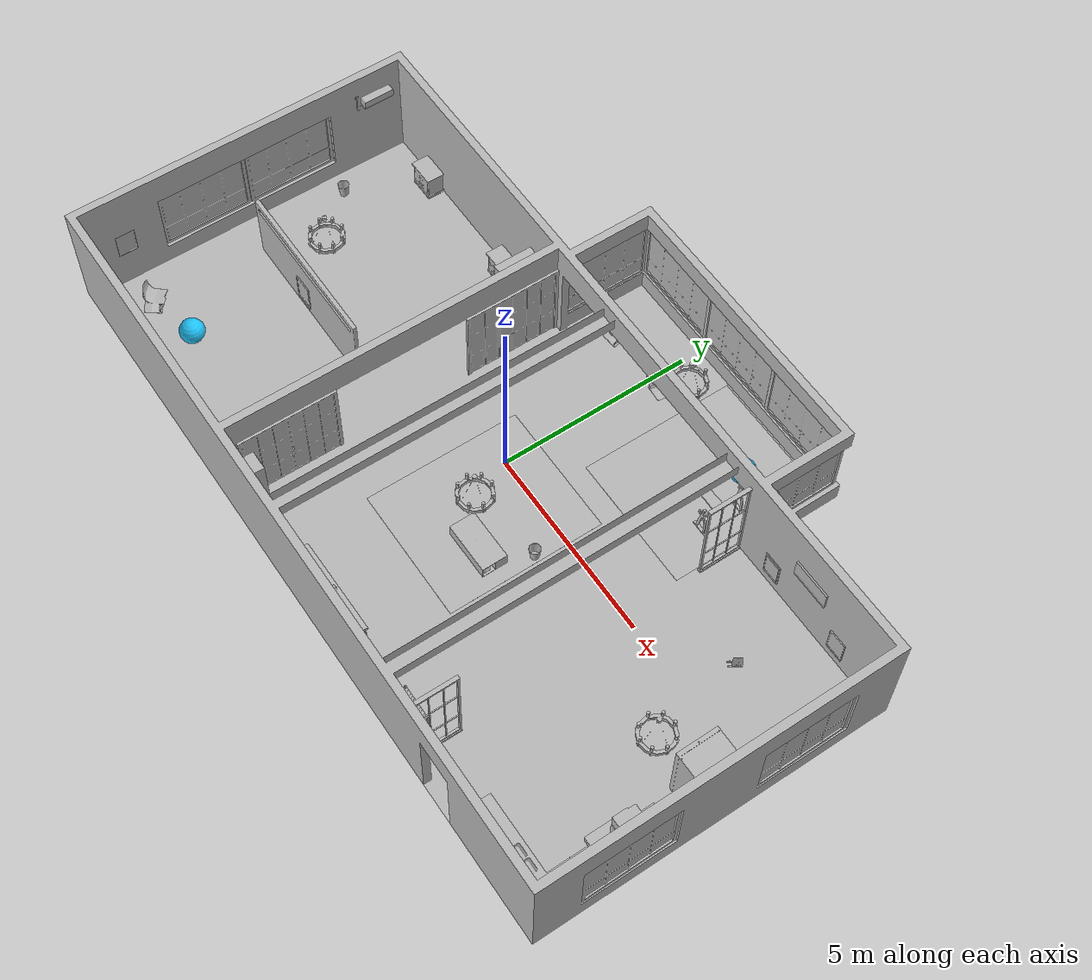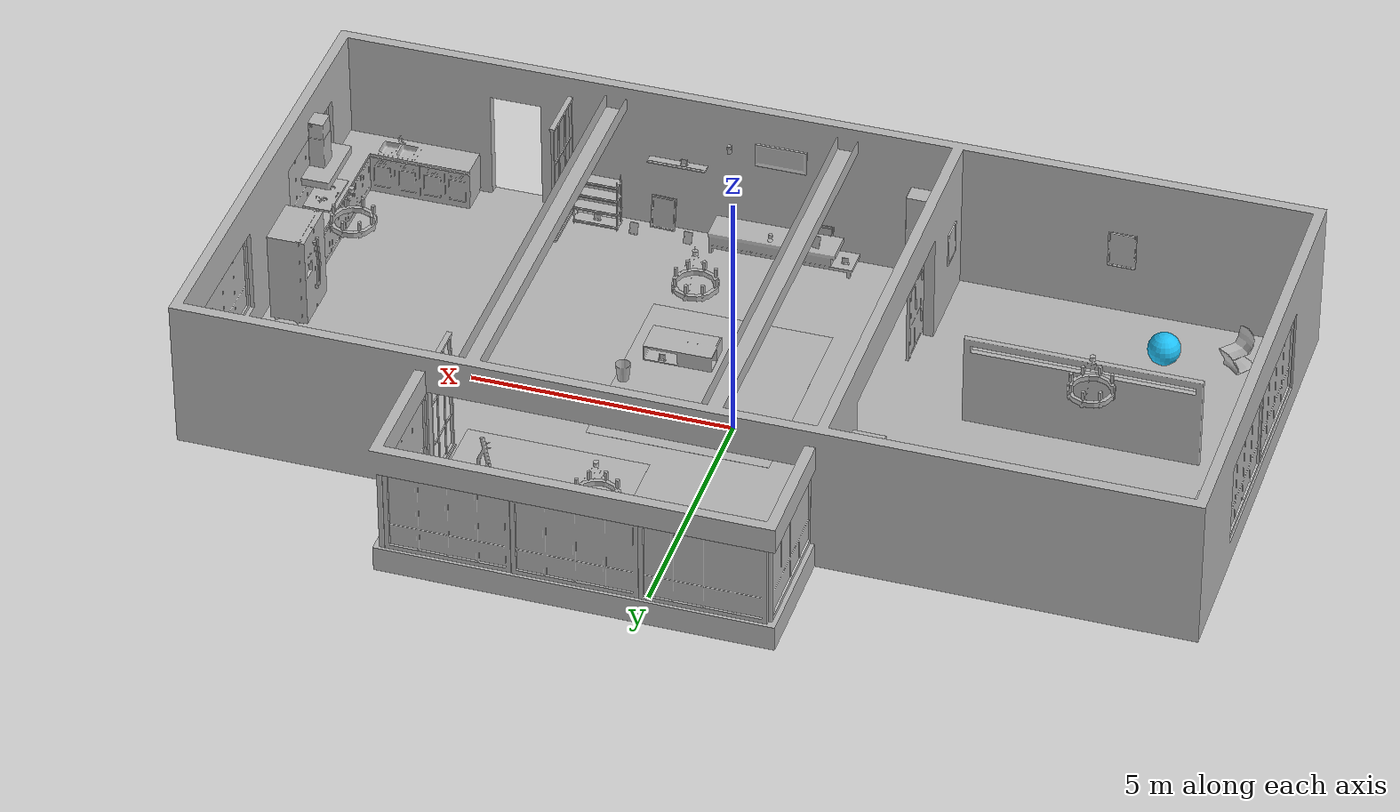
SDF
<sdf version="1.7">
 <world name="default">
  <gravity>0 0 -9.8</gravity>
  <magnetic_field>6e-06 2.3e-05 -4.2e-05</magnetic_field>
  <atmosphere type="adiabatic"/>
  <physics name="default_physics" default="0" type="ode">
   <max_step_size>0.001</max_step_size>
   <real_time_factor>1</real_time_factor>
   <real_time_update_rate>1000</real_time_update_rate>
  </physics>
  <scene>
   <ambient>0.4 0.4 0.4 1</ambient>
   <background>0.7 0.7 0.7 1</background>
   <shadows>1</shadows>
   <grid>0</grid>
   <origin_visual>0</origin_visual>
  </scene>
  <spherical_coordinates>
   <surface_model>EARTH_WGS84</surface_model>
   <latitude_deg>0</latitude_deg>
   <longitude_deg>0</longitude_deg>
   <elevation>0</elevation>
   <heading_deg>0</heading_deg>
  </spherical_coordinates>
  <model name="AirconditionerA_01_001">
   <frame name="aws_robomaker_residential_AirconditionerA_01::__model__" attached_to="aws_robomaker_residential_AirconditionerA_01::link">
    <pose relative_to="__model__">0 0 0 0 -0 0</pose>
   </frame>
   <link name="aws_robomaker_residential_AirconditionerA_01::link">
    <inertial><mass>1</mass></inertial>
    <collision name="collision">
     <geometry>
      <mesh>
       <uri>file://models/aws_robomaker_residential_AirconditionerA_01/meshes/aws_AirconditionerA_01_collision.DAE</uri>
       <scale>1 1 1</scale>
      </mesh>
     </geometry>
    </collision>
    <visual name="visual">
     <geometry>
      <mesh>
       <uri>file://models/aws_robomaker_residential_AirconditionerA_01/meshes/aws_AirconditionerA_01_visual.DAE</uri>
      </mesh>
     </geometry>
     <meta><layer>1</layer></meta>
    </visual>
    <pose relative_to="aws_robomaker_residential_AirconditionerA_01::__model__">0 0 0 0 -0 0</pose>
   </link>
   <static>1</static>
   <pose>-9.19941 2.41123 2.08454 0 -0 0</pose>
  </model>
  <model name="AirconditionerB_01_001">
   <frame name="aws_robomaker_residential_AirconditionerB_01::__model__" attached_to="aws_robomaker_residential_AirconditionerB_01::link">
    <pose relative_to="__model__">0 0 0 0 -0 0</pose>
   </frame>
   <link name="aws_robomaker_residential_AirconditionerB_01::link">
    <inertial>
     <mass>1</mass>
     <inertia><ixx>1</ixx><ixy>0</ixy><ixz>0</ixz><iyy>1</iyy><iyz>0</iyz><izz>1</izz></inertia>
    </inertial>
    <collision name="collision">
     <geometry>
      <mesh>
       <uri>file://models/aws_robomaker_residential_AirconditionerB_01/meshes/aws_AirconditionerB_01_collision.DAE</uri>
       <scale>1 1 1</scale>
      </mesh>
     </geometry>
    </collision>
    <visual name="visual">
     <geometry>
      <mesh>
       <uri>file://models/aws_robomaker_residential_AirconditionerB_01/meshes/aws_AirconditionerB_01_visual.DAE</uri>
      </mesh>
     </geometry>
     <meta><layer>1</layer></meta>
    </visual>
    <pose relative_to="aws_robomaker_residential_AirconditionerB_01::__model__">0 0 0 0 -0 0</pose>
   </link>
   <pose>-2.00466 -5.22661 0.003485 -0 -0 -0</pose>
  </model>
  <model name="Ball_01_001">
   <frame name="aws_robomaker_residential_Ball_01::__model__" attached_to="aws_robomaker_residential_Ball_01::link">
    <pose relative_to="__model__">0 0 0 0 -0 0</pose>
   </frame>
   <link name="aws_robomaker_residential_Ball_01::link">
    <inertial>
     <mass>0.12</mass>
     <inertia>
      <ixx>0.030752</ixx>
      <ixy>0</ixy>
      <ixz>0</ixz>
      <iyy>0.030752</iyy>
      <iyz>0</iyz>
      <izz>0.030752</izz>
     </inertia>
    </inertial>
    <collision name="collision">
     <geometry><sphere><radius>0.31</radius></sphere></geometry>
     <surface>
      <friction><ode><mu>0.85</mu><mu2>0.85</mu2></ode></friction>
      <contact><ode><kd>8500</kd><max_vel>5.1</max_vel></ode></contact>
     </surface>
    </collision>
    <visual name="visual">
     <geometry><sphere><radius>0.31</radius></sphere></geometry>
     <material><diffuse>0.12 0.76 0.97 1</diffuse><ambient>0.03 0.21 0.27 1</ambient></material>
     <meta><layer>1</layer></meta>
    </visual>
    <pose relative_to="aws_robomaker_residential_Ball_01::__model__">0 0 0 0 -0 0</pose>
   </link>
   <pose>3.2955 4.22567 0.31 0 -0 0</pose>
  </model>
  <model name="Ball_01_003">
   <frame name="aws_robomaker_residential_Ball_01::__model__" attached_to="aws_robomaker_residential_Ball_01::link">
    <pose relative_to="__model__">0 0 0 0 -0 0</pose>
   </frame>
   <link name="aws_robomaker_residential_Ball_01::link">
    <inertial>
     <mass>0.12</mass>
     <inertia>
      <ixx>0.030752</ixx>
      <ixy>0</ixy>
      <ixz>0</ixz>
      <iyy>0.030752</iyy>
      <iyz>0</iyz>
      <izz>0.030752</izz>
     </inertia>
    </inertial>
    <collision name="collision">
     <geometry><sphere><radius>0.31</radius></sphere></geometry>
     <surface>
      <friction><ode><mu>0.85</mu><mu2>0.85</mu2></ode></friction>
      <contact><ode><kd>8500</kd><max_vel>5.1</max_vel></ode></contact>
     </surface>
    </collision>
    <visual name="visual">
     <geometry><sphere><radius>0.31</radius></sphere></geometry>
     <material><diffuse>0.12 0.76 0.97 1</diffuse><ambient>0.03 0.21 0.27 1</ambient></material>
     <meta><layer>1</layer></meta>
    </visual>
    <pose relative_to="aws_robomaker_residential_Ball_01::__model__">0 0 0 0 -0 0</pose>
   </link>
   <pose>-6.9455 -4.22174 0.31 0 -0 0</pose>
  </model>
  <model name="NightStand_01_001">
   <frame name="aws_robomaker_residential_NightStand_01::__model__" attached_to="aws_robomaker_residential_NightStand_01::link">
    <pose relative_to="__model__">0 0 0 0 -0 0</pose>
   </frame>
   <link name="aws_robomaker_residential_NightStand_01::link">
    <inertial>
     <mass>13.6</mass>
     <inertia><ixx>0.6165</ixx><ixy>0</ixy><ixz>0</ixz><iyy>1.29664</iyy><iyz>0</iyz><izz>0.7706</izz></inertia>
    </inertial>
    <collision name="collision">
     <geometry>
      <mesh>
       <uri>file://models/aws_robomaker_residential_NightStand_01/meshes/aws_NightStand_01_collision.DAE</uri>
       <scale>1 1 1</scale>
      </mesh>
     </geometry>
    </collision>
    <visual name="visual">
     <geometry>
      <mesh>
       <uri>file://models/aws_robomaker_residential_NightStand_01/meshes/aws_NightStand_01_visual.DAE</uri>
      </mesh>
     </geometry>
     <meta><layer>1</layer></meta>
    </visual>
    <pose relative_to="aws_robomaker_residential_NightStand_01::__model__">0 0 0 0 -0 0</pose>
   </link>
   <static>1</static>
   <pose>-7.72551 2.86042 0.005258 -2e-06 0 0</pose>
  </model>
  <model name="NightStand_01_002">
   <frame name="aws_robomaker_residential_NightStand_01::__model__" attached_to="aws_robomaker_residential_NightStand_01::link">
    <pose relative_to="__model__">0 0 0 0 -0 0</pose>
   </frame>
   <link name="aws_robomaker_residential_NightStand_01::link">
    <inertial>
     <mass>13.6</mass>
     <inertia><ixx>0.6165</ixx><ixy>0</ixy><ixz>0</ixz><iyy>1.29664</iyy><iyz>0</iyz><izz>0.7706</izz></inertia>
    </inertial>
    <collision name="collision">
     <geometry>
      <mesh>
       <uri>file://models/aws_robomaker_residential_NightStand_01/meshes/aws_NightStand_01_collision.DAE</uri>
       <scale>1 1 1</scale>
      </mesh>
     </geometry>
    </collision>
    <visual name="visual">
     <geometry>
      <mesh>
       <uri>file://models/aws_robomaker_residential_NightStand_01/meshes/aws_NightStand_01_visual.DAE</uri>
      </mesh>
     </geometry>
     <meta><layer>1</layer></meta>
    </visual>
    <pose relative_to="aws_robomaker_residential_NightStand_01::__model__">0 0 0 0 -0 0</pose>
   </link>
   <static>1</static>
   <pose>-4.40734 2.86042 0.005256 0 2e-06 0</pose>
  </model>
  <model name="Board_01_001">
   <frame name="aws_robomaker_residential_Board_01::__model__" attached_to="aws_robomaker_residential_Board_01::link">
    <pose relative_to="__model__">0 0 0 0 -0 0</pose>
   </frame>
   <link name="aws_robomaker_residential_Board_01::link">
    <inertial><mass>1</mass></inertial>
    <collision name="collision">
     <geometry>
      <mesh>
       <uri>file://models/aws_robomaker_residential_Board_01/meshes/aws_Board_01_collision.DAE</uri>
       <scale>1 1 1</scale>
      </mesh>
     </geometry>
    </collision>
    <visual name="visual">
     <geometry>
      <mesh><uri>file://models/aws_robomaker_residential_Board_01/meshes/aws_Board_01_visual.DAE</uri></mesh>
     </geometry>
     <meta><layer>2</layer></meta>
    </visual>
    <pose relative_to="aws_robomaker_residential_Board_01::__model__">0 0 0 0 -0 0</pose>
   </link>
   <static>1</static>
   <pose>2.77907 -5.3927 1.53817 0 -0 0</pose>
  </model>
  <model name="ChairD_01_001">
   <frame name="aws_robomaker_residential_ChairD_01::__model__" attached_to="aws_robomaker_residential_ChairD_01::link">
    <pose relative_to="__model__">0 0 0 0 -0 0</pose>
   </frame>
   <link name="aws_robomaker_residential_ChairD_01::link">
    <inertial>
     <mass>4.5</mass>
     <inertia><ixy>0</ixy><ixz>0</ixz><iyz>0</iyz><ixx>0.217</ixx><iyy>0.217</iyy><izz>0.067</izz></inertia>
    </inertial>
    <collision name="collision">
     <geometry>
      <mesh>
       <uri>file://models/aws_robomaker_residential_ChairD_01/meshes/aws_ChairD_01_collision.DAE</uri>
       <scale>1 1 1</scale>
      </mesh>
     </geometry>
    </collision>
    <visual name="visual">
     <geometry>
      <mesh><uri>file://models/aws_robomaker_residential_ChairD_01/meshes/aws_ChairD_01_visual.DAE</uri></mesh>
     </geometry>
     <meta><layer>1</layer></meta>
    </visual>
    <pose relative_to="aws_robomaker_residential_ChairD_01::__model__">0 0 0 0 -0 0</pose>
   </link>
   <pose>-1.38078 4.10446 -0.000249 0 0.000976 0</pose>
  </model>
  <model name="ChairD_01_002">
   <frame name="aws_robomaker_residential_ChairD_01::__model__" attached_to="aws_robomaker_residential_ChairD_01::link">
    <pose relative_to="__model__">0 0 0 0 -0 0</pose>
   </frame>
   <link name="aws_robomaker_residential_ChairD_01::link">
    <inertial>
     <mass>4.5</mass>
     <inertia><ixy>0</ixy><ixz>0</ixz><iyz>0</iyz><ixx>0.217</ixx><iyy>0.217</iyy><izz>0.067</izz></inertia>
    </inertial>
    <collision name="collision">
     <geometry>
      <mesh>
       <uri>file://models/aws_robomaker_residential_ChairD_01/meshes/aws_ChairD_01_collision.DAE</uri>
       <scale>1 1 1</scale>
      </mesh>
     </geometry>
    </collision>
    <visual name="visual">
     <geometry>
      <mesh><uri>file://models/aws_robomaker_residential_ChairD_01/meshes/aws_ChairD_01_visual.DAE</uri></mesh>
     </geometry>
     <meta><layer>1</layer></meta>
    </visual>
    <pose relative_to="aws_robomaker_residential_ChairD_01::__model__">0 0 0 0 -0 0</pose>
   </link>
   <pose>0.325214 4.10446 -0.000249 0 0.000976 -3.13874</pose>
  </model>
  <model name="ChairD_01_003">
   <frame name="aws_robomaker_residential_ChairD_01::__model__" attached_to="aws_robomaker_residential_ChairD_01::link">
    <pose relative_to="__model__">0 0 0 0 -0 0</pose>
   </frame>
   <link name="aws_robomaker_residential_ChairD_01::link">
    <inertial>
     <mass>4.5</mass>
     <inertia><ixy>0</ixy><ixz>0</ixz><iyz>0</iyz><ixx>0.217</ixx><iyy>0.217</iyy><izz>0.067</izz></inertia>
    </inertial>
    <collision name="collision">
     <geometry>
      <mesh>
       <uri>file://models/aws_robomaker_residential_ChairD_01/meshes/aws_ChairD_01_collision.DAE</uri>
       <scale>1 1 1</scale>
      </mesh>
     </geometry>
    </collision>
    <visual name="visual">
     <geometry>
      <mesh><uri>file://models/aws_robomaker_residential_ChairD_01/meshes/aws_ChairD_01_visual.DAE</uri></mesh>
     </geometry>
     <meta><layer>1</layer></meta>
    </visual>
    <pose relative_to="aws_robomaker_residential_ChairD_01::__model__">0 0 0 0 -0 0</pose>
   </link>
   <pose>-8.27078 -4.50446 -0.000249 0 0.000976 0.869673</pose>
  </model>
  <model name="Chandelier_01_001">
   <frame name="aws_robomaker_residential_Chandelier_01::__model__" attached_to="aws_robomaker_residential_Chandelier_01::link">
    <pose relative_to="__model__">0 0 0 0 -0 0</pose>
   </frame>
   <link name="aws_robomaker_residential_Chandelier_01::link">
    <inertial><mass>1</mass></inertial>
    <collision name="collision">
     <geometry>
      <mesh>
       <uri>file://models/aws_robomaker_residential_Chandelier_01/meshes/aws_Chandelier_01_collision.DAE</uri>
       <scale>1 1 1</scale>
      </mesh>
     </geometry>
    </collision>
    <visual name="visual">
     <geometry>
      <mesh>
       <uri>file://models/aws_robomaker_residential_Chandelier_01/meshes/aws_Chandelier_01_visual.DAE</uri>
      </mesh>
     </geometry>
     <meta><layer>2</layer></meta>
    </visual>
    <pose relative_to="aws_robomaker_residential_Chandelier_01::__model__">0 0 0 0 -0 0</pose>
   </link>
   <static>1</static>
   <pose>1.22106 4.15574 1.295 0 -0 0</pose>
  </model>
  <model name="Chandelier_01_002">
   <frame name="aws_robomaker_residential_Chandelier_01::__model__" attached_to="aws_robomaker_residential_Chandelier_01::link">
    <pose relative_to="__model__">0 0 0 0 -0 0</pose>
   </frame>
   <link name="aws_robomaker_residential_Chandelier_01::link">
    <inertial><mass>1</mass></inertial>
    <collision name="collision">
     <geometry>
      <mesh>
       <uri>file://models/aws_robomaker_residential_Chandelier_01/meshes/aws_Chandelier_01_collision.DAE</uri>
       <scale>1 1 1</scale>
      </mesh>
     </geometry>
    </collision>
    <visual name="visual">
     <geometry>
      <mesh>
       <uri>file://models/aws_robomaker_residential_Chandelier_01/meshes/aws_Chandelier_01_visual.DAE</uri>
      </mesh>
     </geometry>
     <meta><layer>2</layer></meta>
    </visual>
    <pose relative_to="aws_robomaker_residential_Chandelier_01::__model__">0 0 0 0 -0 0</pose>
   </link>
   <static>1</static>
   <pose>-6.45106 -0.69204 1.81 0 -0 0</pose>
  </model>
  <model name="Chandelier_01_003">
   <frame name="aws_robomaker_residential_Chandelier_01::__model__" attached_to="aws_robomaker_residential_Chandelier_01::link">
    <pose relative_to="__model__">0 0 0 0 -0 0</pose>
   </frame>
   <link name="aws_robomaker_residential_Chandelier_01::link">
    <inertial><mass>1</mass></inertial>
    <collision name="collision">
     <geometry>
      <mesh>
       <uri>file://models/aws_robomaker_residential_Chandelier_01/meshes/aws_Chandelier_01_collision.DAE</uri>
       <scale>1 1 1</scale>
      </mesh>
     </geometry>
    </collision>
    <visual name="visual">
     <geometry>
      <mesh>
       <uri>file://models/aws_robomaker_residential_Chandelier_01/meshes/aws_Chandelier_01_visual.DAE</uri>
      </mesh>
     </geometry>
     <meta><layer>2</layer></meta>
    </visual>
    <pose relative_to="aws_robomaker_residential_Chandelier_01::__model__">0 0 0 0 -0 0</pose>
   </link>
   <static>1</static>
   <pose>7.82406 -1.59 1.751 0 -0 0</pose>
  </model>
  <model name="Chandelier_01_004">
   <frame name="aws_robomaker_residential_Chandelier_01::__model__" attached_to="aws_robomaker_residential_Chandelier_01::link">
    <pose relative_to="__model__">0 0 0 0 -0 0</pose>
   </frame>
   <link name="aws_robomaker_residential_Chandelier_01::link">
    <inertial><mass>1</mass></inertial>
    <collision name="collision">
     <geometry>
      <mesh>
       <uri>file://models/aws_robomaker_residential_Chandelier_01/meshes/aws_Chandelier_01_collision.DAE</uri>
       <scale>1 1 1</scale>
      </mesh>
     </geometry>
    </collision>
    <visual name="visual">
     <geometry>
      <mesh>
       <uri>file://models/aws_robomaker_residential_Chandelier_01/meshes/aws_Chandelier_01_visual.DAE</uri>
      </mesh>
     </geometry>
     <meta><layer>2</layer></meta>
    </visual>
    <pose relative_to="aws_robomaker_residential_Chandelier_01::__model__">0 0 0 0 -0 0</pose>
   </link>
   <static>1</static>
   <pose>1.22106 -1.59204 1.7873 0 -0 0</pose>
  </model>
  <model name="Carpet_01_001">
   <frame name="aws_robomaker_residential_Carpet_01::__model__" attached_to="aws_robomaker_residential_Carpet_01::link">
    <pose relative_to="__model__">0 0 0 0 -0 0</pose>
   </frame>
   <link name="aws_robomaker_residential_Carpet_01::link">
    <inertial><mass>8.1</mass></inertial>
    <collision name="collision">
     <geometry>
      <mesh>
       <uri>file://models/aws_robomaker_residential_Carpet_01/meshes/aws_Carpet_01_collision.DAE</uri>
       <scale>1 1 0.95</scale>
      </mesh>
     </geometry>
     <pose>0 0 -0.01 0 -0 0</pose>
    </collision>
    <visual name="visual">
     <geometry>
      <mesh><uri>file://models/aws_robomaker_residential_Carpet_01/meshes/aws_Carpet_01_visual.DAE</uri></mesh>
     </geometry>
     <meta><layer>1</layer></meta>
    </visual>
    <pose relative_to="aws_robomaker_residential_Carpet_01::__model__">0 0 0 0 -0 0</pose>
   </link>
   <static>1</static>
   <pose>0.78505 -1.10665 0.001106 0 -0 0</pose>
  </model>
  <model name="Carpet_01_002">
   <frame name="aws_robomaker_residential_Carpet_01::__model__" attached_to="aws_robomaker_residential_Carpet_01::link">
    <pose relative_to="__model__">0 0 0 0 -0 0</pose>
   </frame>
   <link name="aws_robomaker_residential_Carpet_01::link">
    <inertial><mass>8.1</mass></inertial>
    <collision name="collision">
     <geometry>
      <mesh>
       <uri>file://models/aws_robomaker_residential_Carpet_01/meshes/aws_Carpet_01_collision.DAE</uri>
       <scale>1 1 0.95</scale>
      </mesh>
     </geometry>
     <pose>0 0 -0.01 0 -0 0</pose>
    </collision>
    <visual name="visual">
     <geometry>
      <mesh><uri>file://models/aws_robomaker_residential_Carpet_01/meshes/aws_Carpet_01_visual.DAE</uri></mesh>
     </geometry>
     <meta><layer>1</layer></meta>
    </visual>
    <pose relative_to="aws_robomaker_residential_Carpet_01::__model__">0 0 0 0 -0 0</pose>
   </link>
   <static>1</static>
   <pose>2.85405 3.45 0.000585 0 -0 0</pose>
  </model>
  <model name="SecurityCamera_01_001">
   <frame name="aws_robomaker_residential_SecurityCamera_01::__model__" attached_to="aws_robomaker_residential_SecurityCamera_01::link">
    <pose relative_to="__model__">0 0 0 0 -0 0</pose>
   </frame>
   <link name="aws_robomaker_residential_SecurityCamera_01::link">
    <inertial>
     <mass>1</mass>
     <inertia>
      <ixx>18.2222</ixx>
      <ixy>0</ixy>
      <ixz>0</ixz>
      <iyy>18.2222</iyy>
      <iyz>0</iyz>
      <izz>0.0018767</izz>
     </inertia>
    </inertial>
    <collision name="collision">
     <geometry>
      <mesh>
       <uri>file://models/aws_robomaker_residential_SecurityCamera_01/meshes/aws_SecurityCamera_01_collision.DAE</uri>
       <scale>1 1 1</scale>
      </mesh>
     </geometry>
    </collision>
    <visual name="visual">
     <geometry>
      <mesh>
       <uri>file://models/aws_robomaker_residential_SecurityCamera_01/meshes/aws_SecurityCamera_01_visual.DAE</uri>
      </mesh>
     </geometry>
     <meta><layer>2</layer></meta>
    </visual>
    <pose relative_to="aws_robomaker_residential_SecurityCamera_01::__model__">0 0 0 0 -0 0</pose>
   </link>
   <pose>0.842134 -4.99629 0.492555 1e-06 -2e-06 -2.84104</pose>
  </model>
  <model name="CoffeeTable_01_001">
   <frame name="aws_robomaker_residential_CoffeeTable_01::__model__" attached_to="aws_robomaker_residential_CoffeeTable_01::link">
    <pose relative_to="__model__">0 0 0 0 -0 0</pose>
   </frame>
   <link name="aws_robomaker_residential_CoffeeTable_01::link">
    <inertial>
     <mass>21.7</mass>
     <inertia><ixx>0.81375</ixx><ixy>0</ixy><ixz>0</ixz><iyy>2.76675</iyy><iyz>0</iyz><izz>3.254</izz></inertia>
    </inertial>
    <collision name="collision">
     <geometry>
      <mesh>
       <uri>file://models/aws_robomaker_residential_CoffeeTable_01/meshes/aws_CoffeeTable_01_collision.DAE</uri>
       <scale>1 1 1</scale>
      </mesh>
     </geometry>
     <surface><contact><ode><max_vel>0.01</max_vel></ode></contact></surface>
    </collision>
    <visual name="visual">
     <geometry>
      <mesh>
       <uri>file://models/aws_robomaker_residential_CoffeeTable_01/meshes/aws_CoffeeTable_01_visual.DAE</uri>
      </mesh>
     </geometry>
     <meta><layer>1</layer></meta>
    </visual>
    <pose relative_to="aws_robomaker_residential_CoffeeTable_01::__model__">0 0 0 0 -0 0</pose>
   </link>
   <static>1</static>
   <pose>1.5123 -1.73344 0.041983 0 -0 0.01</pose>
  </model>
  <model name="CookingBench_01_001">
   <frame name="aws_robomaker_residential_CookingBench_01::__model__" attached_to="aws_robomaker_residential_CookingBench_01::link">
    <pose relative_to="__model__">0 0 0 0 -0 0</pose>
   </frame>
   <link name="aws_robomaker_residential_CookingBench_01::link">
    <inertial><mass>1</mass></inertial>
    <collision name="collision">
     <geometry>
      <mesh>
       <uri>file://models/aws_robomaker_residential_CookingBench_01/meshes/aws_CookingBench_01_collision.DAE</uri>
       <scale>1 1 1</scale>
      </mesh>
     </geometry>
    </collision>
    <visual name="visual">
     <geometry>
      <mesh>
       <uri>file://models/aws_robomaker_residential_CookingBench_01/meshes/aws_CookingBench_01_visual.DAE</uri>
      </mesh>
     </geometry>
     <meta><layer>1</layer></meta>
    </visual>
    <pose relative_to="aws_robomaker_residential_CookingBench_01::__model__">0 0 0 0 -0 0</pose>
   </link>
   <pose>9.03838 -3.35114 0.90361 0 -0 3.13713</pose>
   <static>1</static>
  </model>
  <model name="FitnessEquipment_01_001">
   <frame name="aws_robomaker_residential_FitnessEquipment_01::__model__" attached_to="aws_robomaker_residential_FitnessEquipment_01::link">
    <pose relative_to="__model__">0 0 0 0 -0 0</pose>
   </frame>
   <link name="aws_robomaker_residential_FitnessEquipment_01::link">
    <inertial><mass>80</mass></inertial>
    <collision name="collision">
     <geometry>
      <mesh>
       <uri>file://models/aws_robomaker_residential_FitnessEquipment_01/meshes/aws_FitnessEquipment_01_collision.DAE</uri>
       <scale>1 1 1</scale>
      </mesh>
     </geometry>
    </collision>
    <visual name="visual">
     <geometry>
      <mesh>
       <uri>file://models/aws_robomaker_residential_FitnessEquipment_01/meshes/aws_FitnessEquipment_01_visual.DAE</uri>
      </mesh>
     </geometry>
     <meta><layer>1</layer></meta>
    </visual>
    <pose relative_to="aws_robomaker_residential_FitnessEquipment_01::__model__">0 0 0 0 -0 0</pose>
   </link>
   <static>1</static>
   <pose>3.48472 3.1691 0.003168 0 -0 0</pose>
  </model>
  <model name="FoldingDoor_01_001">
   <frame name="aws_robomaker_residential_FoldingDoor_01::__model__" attached_to="aws_robomaker_residential_FoldingDoor_01::link">
    <pose relative_to="__model__">0 0 0 0 -0 0</pose>
   </frame>
   <link name="aws_robomaker_residential_FoldingDoor_01::link">
    <inertial><mass>1</mass></inertial>
    <collision name="collision">
     <geometry>
      <mesh>
       <uri>file://models/aws_robomaker_residential_FoldingDoor_01/meshes/aws_FoldingDoor_01_collision.DAE</uri>
       <scale>1 1 1</scale>
      </mesh>
     </geometry>
    </collision>
    <visual name="visual">
     <geometry>
      <mesh>
       <uri>file://models/aws_robomaker_residential_FoldingDoor_01/meshes/aws_FoldingDoor_01_visual.DAE</uri>
      </mesh>
     </geometry>
     <meta><layer>2</layer></meta>
    </visual>
    <pose relative_to="aws_robomaker_residential_FoldingDoor_01::__model__">0 0 0 0 -0 0</pose>
   </link>
   <static>1</static>
   <pose>-2.4611 1.84422 0.041881 0 -0 0</pose>
  </model>
  <model name="FoldingDoor_01_002">
   <frame name="aws_robomaker_residential_FoldingDoor_01::__model__" attached_to="aws_robomaker_residential_FoldingDoor_01::link">
    <pose relative_to="__model__">0 0 0 0 -0 0</pose>
   </frame>
   <link name="aws_robomaker_residential_FoldingDoor_01::link">
    <inertial><mass>1</mass></inertial>
    <collision name="collision">
     <geometry>
      <mesh>
       <uri>file://models/aws_robomaker_residential_FoldingDoor_01/meshes/aws_FoldingDoor_01_collision.DAE</uri>
       <scale>1 1 1</scale>
      </mesh>
     </geometry>
    </collision>
    <visual name="visual">
     <geometry>
      <mesh>
       <uri>file://models/aws_robomaker_residential_FoldingDoor_01/meshes/aws_FoldingDoor_01_visual.DAE</uri>
      </mesh>
     </geometry>
     <meta><layer>2</layer></meta>
    </visual>
    <pose relative_to="aws_robomaker_residential_FoldingDoor_01::__model__">0 0 0 0 -0 0</pose>
   </link>
   <static>1</static>
   <pose>-2.4611 -4.05332 0.041881 0 -0 0</pose>
  </model>
  <model name="HouseWallB_01_001">
   <frame name="aws_robomaker_residential_HouseWallB_01::__model__" attached_to="aws_robomaker_residential_HouseWallB_01::link">
    <pose relative_to="__model__">0 0 0 0 -0 0</pose>
   </frame>
   <link name="aws_robomaker_residential_HouseWallB_01::link">
    <inertial><mass>1</mass></inertial>
    <collision name="collision">
     <geometry>
      <mesh>
       <uri>file://models/aws_robomaker_residential_HouseWallB_01/meshes/aws_HouseWallB_01_collision.DAE</uri>
       <scale>1 1 1</scale>
      </mesh>
     </geometry>
    </collision>
    <visual name="visual">
     <geometry>
      <mesh>
       <uri>file://models/aws_robomaker_residential_HouseWallB_01/meshes/aws_HouseWallB_01_visual.DAE</uri>
      </mesh>
     </geometry>
     <meta><layer>2</layer></meta>
    </visual>
    <pose relative_to="aws_robomaker_residential_HouseWallB_01::__model__">0 0 0 0 -0 0</pose>
   </link>
   <static>1</static>
  </model>
  <model name="FloorB_01_001">
   <frame name="aws_robomaker_residential_FloorB_01::__model__" attached_to="aws_robomaker_residential_FloorB_01::link">
    <pose relative_to="__model__">0 0 0 0 -0 0</pose>
   </frame>
   <link name="aws_robomaker_residential_FloorB_01::link">
    <inertial><mass>100</mass></inertial>
    <collision name="collision">
     <geometry>
      <mesh>
       <uri>file://models/aws_robomaker_residential_FloorB_01/meshes/aws_FloorB_01_collision.DAE</uri>
       <scale>1 1 0.9</scale>
      </mesh>
     </geometry>
     <surface><friction><ode><mu>0.6</mu><mu2>0.6</mu2></ode></friction></surface>
    </collision>
    <visual name="visual">
     <geometry>
      <mesh><uri>file://models/aws_robomaker_residential_FloorB_01/meshes/aws_FloorB_01_visual.DAE</uri></mesh>
     </geometry>
     <meta><layer>1</layer></meta>
    </visual>
    <pose relative_to="aws_robomaker_residential_FloorB_01::__model__">0 0 0 0 -0 0</pose>
   </link>
   <static>1</static>
  </model>
  <model name="FoldingDoor_02_001">
   <frame name="aws_robomaker_residential_FoldingDoor_02::__model__" attached_to="aws_robomaker_residential_FoldingDoor_02::link">
    <pose relative_to="__model__">0 0 0 0 -0 0</pose>
   </frame>
   <link name="aws_robomaker_residential_FoldingDoor_02::link">
    <inertial><mass>1</mass></inertial>
    <collision name="collision">
     <geometry>
      <mesh>
       <uri>file://models/aws_robomaker_residential_FoldingDoor_02/meshes/aws_FoldingDoor_02_collision.DAE</uri>
       <scale>1 1 1</scale>
      </mesh>
     </geometry>
    </collision>
    <visual name="visual">
     <geometry>
      <mesh>
       <uri>file://models/aws_robomaker_residential_FoldingDoor_02/meshes/aws_FoldingDoor_02_visual.DAE</uri>
      </mesh>
     </geometry>
     <meta><layer>2</layer></meta>
    </visual>
    <pose relative_to="aws_robomaker_residential_FoldingDoor_02::__model__">0 0 0 0 -0 0</pose>
   </link>
   <static>1</static>
   <pose>4.67423 2.46451 0 0 -0 3.14159</pose>
  </model>
  <model name="FoldingDoor_02_002">
   <frame name="aws_robomaker_residential_FoldingDoor_02::__model__" attached_to="aws_robomaker_residential_FoldingDoor_02::link">
    <pose relative_to="__model__">0 0 0 0 -0 0</pose>
   </frame>
   <link name="aws_robomaker_residential_FoldingDoor_02::link">
    <inertial><mass>1</mass></inertial>
    <collision name="collision">
     <geometry>
      <mesh>
       <uri>file://models/aws_robomaker_residential_FoldingDoor_02/meshes/aws_FoldingDoor_02_collision.DAE</uri>
       <scale>1 1 1</scale>
      </mesh>
     </geometry>
    </collision>
    <visual name="visual">
     <geometry>
      <mesh>
       <uri>file://models/aws_robomaker_residential_FoldingDoor_02/meshes/aws_FoldingDoor_02_visual.DAE</uri>
      </mesh>
     </geometry>
     <meta><layer>2</layer></meta>
    </visual>
    <pose relative_to="aws_robomaker_residential_FoldingDoor_02::__model__">0 0 0 0 -0 0</pose>
   </link>
   <static>1</static>
   <pose>4.8912 -4.84968 0 0 -0 0</pose>
  </model>
  <model name="KitchenCabinet_01_001">
   <frame name="aws_robomaker_residential_KitchenCabinet_01::__model__" attached_to="aws_robomaker_residential_KitchenCabinet_01::link">
    <pose relative_to="__model__">0 0 0 0 -0 0</pose>
   </frame>
   <link name="aws_robomaker_residential_KitchenCabinet_01::link">
    <inertial><mass>1</mass></inertial>
    <collision name="collision">
     <geometry>
      <mesh>
       <uri>file://models/aws_robomaker_residential_KitchenCabinet_01/meshes/aws_KitchenCabinet_01_collision.DAE</uri>
       <scale>1 1 1</scale>
      </mesh>
     </geometry>
    </collision>
    <visual name="visual">
     <geometry>
      <mesh>
       <uri>file://models/aws_robomaker_residential_KitchenCabinet_01/meshes/aws_KitchenCabinet_01_visual.DAE</uri>
      </mesh>
     </geometry>
     <meta><layer>1</layer></meta>
    </visual>
    <pose relative_to="aws_robomaker_residential_KitchenCabinet_01::__model__">0 0 0 0 -0 0</pose>
   </link>
   <static>1</static>
   <pose>8.00201 -3.83651 0.012068 0 0 -3.14</pose>
  </model>
  <model name="LightC_01_001">
   <frame name="aws_robomaker_residential_LightC_01::__model__" attached_to="aws_robomaker_residential_LightC_01::link">
    <pose relative_to="__model__">0 0 0 0 -0 0</pose>
   </frame>
   <link name="aws_robomaker_residential_LightC_01::link">
    <inertial><mass>1</mass></inertial>
    <collision name="collision">
     <geometry>
      <mesh>
       <uri>file://models/aws_robomaker_residential_LightC_01/meshes/aws_LightC_01_collision.DAE</uri>
       <scale>1 1 1</scale>
      </mesh>
     </geometry>
    </collision>
    <visual name="visual">
     <geometry>
      <mesh><uri>file://models/aws_robomaker_residential_LightC_01/meshes/aws_LightC_01_visual.DAE</uri></mesh>
     </geometry>
     <meta><layer>2</layer></meta>
    </visual>
    <pose relative_to="aws_robomaker_residential_LightC_01::__model__">0 0 0 0 -0 0</pose>
   </link>
   <static>1</static>
   <pose>1.76957 -5.44437 2 0 -0 0</pose>
  </model>
  <model name="LightC_01_002">
   <frame name="aws_robomaker_residential_LightC_01::__model__" attached_to="aws_robomaker_residential_LightC_01::link">
    <pose relative_to="__model__">0 0 0 0 -0 0</pose>
   </frame>
   <link name="aws_robomaker_residential_LightC_01::link">
    <inertial><mass>1</mass></inertial>
    <collision name="collision">
     <geometry>
      <mesh>
       <uri>file://models/aws_robomaker_residential_LightC_01/meshes/aws_LightC_01_collision.DAE</uri>
       <scale>1 1 1</scale>
      </mesh>
     </geometry>
    </collision>
    <visual name="visual">
     <geometry>
      <mesh><uri>file://models/aws_robomaker_residential_LightC_01/meshes/aws_LightC_01_visual.DAE</uri></mesh>
     </geometry>
     <meta><layer>2</layer></meta>
    </visual>
    <pose relative_to="aws_robomaker_residential_LightC_01::__model__">0 0 0 0 -0 0</pose>
   </link>
   <static>1</static>
   <pose>-0.138245 -5.44437 2 0 -0 0</pose>
  </model>
  <model name="PortraitA_01">
   <frame name="aws_robomaker_residential_PortraitA_01::__model__" attached_to="aws_robomaker_residential_PortraitA_01::link">
    <pose relative_to="__model__">0 0 0 0 -0 0</pose>
   </frame>
   <link name="aws_robomaker_residential_PortraitA_01::link">
    <inertial><mass>1</mass></inertial>
    <collision name="collision">
     <geometry>
      <mesh>
       <uri>file://models/aws_robomaker_residential_PortraitA_01/meshes/aws_PortraitA_01_collision.DAE</uri>
       <scale>1 1 1</scale>
      </mesh>
     </geometry>
    </collision>
    <visual name="visual">
     <geometry>
      <mesh>
       <uri>file://models/aws_robomaker_residential_PortraitA_01/meshes/aws_PortraitA_01_visual.DAE</uri>
      </mesh>
     </geometry>
     <meta><layer>2</layer></meta>
    </visual>
    <pose relative_to="aws_robomaker_residential_PortraitA_01::__model__">0 0 0 0 -0 0</pose>
   </link>
   <static>1</static>
   <pose>-2.71236 -4.81754 1 0 -0 1.5668</pose>
  </model>
  <model name="PortraitB_01">
   <frame name="aws_robomaker_residential_PortraitB_01::__model__" attached_to="aws_robomaker_residential_PortraitB_01::link">
    <pose relative_to="__model__">0 0 0 0 -0 0</pose>
   </frame>
   <link name="aws_robomaker_residential_PortraitB_01::link">
    <inertial><mass>1</mass></inertial>
    <collision name="collision">
     <geometry>
      <mesh>
       <uri>file://models/aws_robomaker_residential_PortraitB_01/meshes/aws_PortraitB_01_collision.DAE</uri>
       <scale>1 1 1</scale>
      </mesh>
     </geometry>
    </collision>
    <visual name="visual">
     <geometry>
      <mesh>
       <uri>file://models/aws_robomaker_residential_PortraitB_01/meshes/aws_PortraitB_01_visual.DAE</uri>
      </mesh>
     </geometry>
     <meta><layer>2</layer></meta>
    </visual>
    <pose relative_to="aws_robomaker_residential_PortraitB_01::__model__">0 0 0 0 -0 0</pose>
   </link>
   <static>1</static>
   <pose>0 -5.42963 0 -0.076901 0 -3.11672</pose>
  </model>
  <model name="PortraitB_02">
   <frame name="aws_robomaker_residential_PortraitB_02::__model__" attached_to="aws_robomaker_residential_PortraitB_02::link">
    <pose relative_to="__model__">0 0 0 0 -0 0</pose>
   </frame>
   <link name="aws_robomaker_residential_PortraitB_02::link">
    <inertial><mass>1</mass></inertial>
    <collision name="collision">
     <geometry>
      <mesh>
       <uri>file://models/aws_robomaker_residential_PortraitB_02/meshes/aws_PortraitB_01_collision.DAE</uri>
       <scale>1 1 1</scale>
      </mesh>
     </geometry>
    </collision>
    <visual name="visual">
     <geometry>
      <mesh>
       <uri>file://models/aws_robomaker_residential_PortraitB_02/meshes/aws_PortraitB_01_visual.DAE</uri>
      </mesh>
     </geometry>
     <meta><layer>2</layer></meta>
    </visual>
    <pose relative_to="aws_robomaker_residential_PortraitB_02::__model__">0 0 0 0 -0 0</pose>
   </link>
   <static>1</static>
   <pose>5.73702 3.08031 0.3 0 -0 0</pose>
  </model>
  <model name="PortraitB_03">
   <frame name="aws_robomaker_residential_PortraitB_03::__model__" attached_to="aws_robomaker_residential_PortraitB_03::link">
    <pose relative_to="__model__">0 0 0 0 -0 0</pose>
   </frame>
   <link name="aws_robomaker_residential_PortraitB_03::link">
    <inertial><mass>1</mass></inertial>
    <collision name="collision">
     <geometry>
      <mesh>
       <uri>file://models/aws_robomaker_residential_PortraitB_03/meshes/aws_PortraitB_01_collision.DAE</uri>
       <scale>1 1 1</scale>
      </mesh>
     </geometry>
    </collision>
    <visual name="visual">
     <geometry>
      <mesh>
       <uri>file://models/aws_robomaker_residential_PortraitB_03/meshes/aws_PortraitB_01_visual.DAE</uri>
      </mesh>
     </geometry>
     <meta><layer>2</layer></meta>
    </visual>
    <pose relative_to="aws_robomaker_residential_PortraitB_03::__model__">0 0 0 0 -0 0</pose>
   </link>
   <static>1</static>
   <pose>3.07138 -5.34937 0.005494 -0.168428 -0 3.10423</pose>
  </model>
  <model name="PortraitA_02">
   <frame name="aws_robomaker_residential_PortraitA_02::__model__" attached_to="aws_robomaker_residential_PortraitA_02::link">
    <pose relative_to="__model__">0 0 0 0 -0 0</pose>
   </frame>
   <link name="aws_robomaker_residential_PortraitA_02::link">
    <inertial><mass>1</mass></inertial>
    <collision name="collision">
     <geometry>
      <mesh>
       <uri>file://models/aws_robomaker_residential_PortraitA_02/meshes/aws_PortraitA_01_collision.DAE</uri>
       <scale>1 1 1</scale>
      </mesh>
     </geometry>
    </collision>
    <visual name="visual">
     <geometry>
      <mesh>
       <uri>file://models/aws_robomaker_residential_PortraitA_02/meshes/aws_PortraitA_01_visual.DAE</uri>
      </mesh>
     </geometry>
     <meta><layer>2</layer></meta>
    </visual>
    <pose relative_to="aws_robomaker_residential_PortraitA_02::__model__">0 0 0 0 -0 0</pose>
   </link>
   <static>1</static>
   <pose>7.93702 3.08031 0.3 0 -0 3.14</pose>
  </model>
  <model name="PortraitC_01">
   <frame name="aws_robomaker_residential_PortraitC_01::__model__" attached_to="aws_robomaker_residential_PortraitC_01::link">
    <pose relative_to="__model__">0 0 0 0 -0 0</pose>
   </frame>
   <link name="aws_robomaker_residential_PortraitC_01::link">
    <inertial><mass>1</mass></inertial>
    <collision name="collision">
     <geometry>
      <mesh>
       <uri>file://models/aws_robomaker_residential_PortraitC_01/meshes/aws_PortraitC_01_collision.DAE</uri>
       <scale>1 1 1</scale>
      </mesh>
     </geometry>
    </collision>
    <visual name="visual">
     <geometry>
      <mesh>
       <uri>file://models/aws_robomaker_residential_PortraitC_01/meshes/aws_PortraitC_01_visual.DAE</uri>
      </mesh>
     </geometry>
     <meta><layer>2</layer></meta>
    </visual>
    <pose relative_to="aws_robomaker_residential_PortraitC_01::__model__">0 0 0 0 -0 0</pose>
   </link>
   <static>1</static>
   <pose>-9.2949 -4.52608 1 0 -0 1.55473</pose>
  </model>
  <model name="PortraitD_01">
   <frame name="aws_robomaker_residential_PortraitD_01::__model__" attached_to="aws_robomaker_residential_PortraitD_01::link">
    <pose relative_to="__model__">0 0 0 0 -0 0</pose>
   </frame>
   <link name="aws_robomaker_residential_PortraitD_01::link">
    <inertial><mass>1.5</mass></inertial>
    <collision name="collision">
     <geometry>
      <mesh>
       <uri>file://models/aws_robomaker_residential_PortraitD_01/meshes/aws_PortraitD_01_collision.DAE</uri>
       <scale>1 1 1</scale>
      </mesh>
     </geometry>
    </collision>
    <visual name="visual">
     <geometry>
      <mesh>
       <uri>file://models/aws_robomaker_residential_PortraitD_01/meshes/aws_PortraitD_01_visual.DAE</uri>
      </mesh>
     </geometry>
     <meta><layer>2</layer></meta>
    </visual>
    <pose relative_to="aws_robomaker_residential_PortraitD_01::__model__">0 0 0 0 -0 0</pose>
   </link>
   <static>1</static>
   <pose>0.789763 -5.47872 1.8 0 -0 3.13853</pose>
  </model>
  <model name="PortraitD_02">
   <frame name="aws_robomaker_residential_PortraitD_02::__model__" attached_to="aws_robomaker_residential_PortraitD_02::link">
    <pose relative_to="__model__">0 0 0 0 -0 0</pose>
   </frame>
   <link name="aws_robomaker_residential_PortraitD_02::link">
    <inertial><mass>1.5</mass></inertial>
    <collision name="collision">
     <geometry>
      <mesh>
       <uri>file://models/aws_robomaker_residential_PortraitD_02/meshes/aws_PortraitD_01_collision.DAE</uri>
       <scale>1 1 1</scale>
      </mesh>
     </geometry>
    </collision>
    <visual name="visual">
     <geometry>
      <mesh>
       <uri>file://models/aws_robomaker_residential_PortraitD_02/meshes/aws_PortraitD_01_visual.DAE</uri>
      </mesh>
     </geometry>
     <meta><layer>2</layer></meta>
    </visual>
    <pose relative_to="aws_robomaker_residential_PortraitD_02::__model__">0 0 0 0 -0 0</pose>
   </link>
   <static>1</static>
   <pose>6.87018 3.08031 1.48844 0 -0 0</pose>
  </model>
  <model name="PortraitE_01">
   <frame name="aws_robomaker_residential_PortraitE_01::__model__" attached_to="aws_robomaker_residential_PortraitE_01::link">
    <pose relative_to="__model__">0 0 0 0 -0 0</pose>
   </frame>
   <link name="aws_robomaker_residential_PortraitE_01::link">
    <inertial><mass>1</mass></inertial>
    <collision name="collision">
     <geometry>
      <mesh>
       <uri>file://models/aws_robomaker_residential_PortraitE_01/meshes/aws_PortraitE_01_collision.DAE</uri>
       <scale>1 1 1</scale>
      </mesh>
     </geometry>
    </collision>
    <visual name="visual">
     <geometry>
      <mesh>
       <uri>file://models/aws_robomaker_residential_PortraitE_01/meshes/aws_PortraitE_01_visual.DAE</uri>
      </mesh>
     </geometry>
     <meta><layer>2</layer></meta>
    </visual>
    <pose relative_to="aws_robomaker_residential_PortraitE_01::__model__">0 0 0 0 -0 0</pose>
   </link>
   <static>1</static>
   <pose>-5.77309 -5.49247 1 0 -0 3.13263</pose>
  </model>
  <model name="PortraitE_02">
   <frame name="aws_robomaker_residential_PortraitE_02::__model__" attached_to="aws_robomaker_residential_PortraitE_02::link">
    <pose relative_to="__model__">0 0 0 0 -0 0</pose>
   </frame>
   <link name="aws_robomaker_residential_PortraitE_02::link">
    <inertial><mass>1</mass></inertial>
    <collision name="collision">
     <geometry>
      <mesh>
       <uri>file://models/aws_robomaker_residential_PortraitE_02/meshes/aws_PortraitE_01_collision.DAE</uri>
       <scale>1 1 1</scale>
      </mesh>
     </geometry>
    </collision>
    <visual name="visual">
     <geometry>
      <mesh>
       <uri>file://models/aws_robomaker_residential_PortraitE_02/meshes/aws_PortraitE_01_visual.DAE</uri>
      </mesh>
     </geometry>
     <meta><layer>2</layer></meta>
    </visual>
    <pose relative_to="aws_robomaker_residential_PortraitE_02::__model__">0 0 0 0 -0 0</pose>
   </link>
   <static>1</static>
   <pose>-6.19302 -1.59021 0.3 0 -0 0.00429</pose>
  </model>
  <model name="DeskPortraitA_01">
   <frame name="aws_robomaker_residential_DeskPortraitA_01::__model__" attached_to="aws_robomaker_residential_DeskPortraitA_01::link">
    <pose relative_to="__model__">0 0 0 0 -0 0</pose>
   </frame>
   <link name="aws_robomaker_residential_DeskPortraitA_01::link">
    <inertial>
     <mass>1</mass>
     <inertia><ixx>0.0835</ixx><ixy>0</ixy><ixz>0</ixz><iyy>0.16</iyy><iyz>0</iyz><izz>0.08347</izz></inertia>
    </inertial>
    <collision name="collision">
     <geometry>
      <mesh>
       <uri>file://models/aws_robomaker_residential_DeskPortraitA_01/meshes/aws_DeskPortraitA_01_collision.DAE</uri>
       <scale>1 1 1</scale>
      </mesh>
     </geometry>
    </collision>
    <visual name="visual">
     <geometry>
      <mesh>
       <uri>file://models/aws_robomaker_residential_DeskPortraitA_01/meshes/aws_DeskPortraitA_01_visual.DAE</uri>
      </mesh>
     </geometry>
     <meta><layer>1</layer></meta>
    </visual>
    <pose relative_to="aws_robomaker_residential_DeskPortraitA_01::__model__">0 0 0 0 -0 0</pose>
   </link>
   <pose>-0.036864 -5.11016 0.492604 -0.000543 -0 2.92778</pose>
  </model>
  <model name="DeskPortraitA_02">
   <frame name="aws_robomaker_residential_DeskPortraitA_02::__model__" attached_to="aws_robomaker_residential_DeskPortraitA_02::link">
    <pose relative_to="__model__">0 0 0 0 -0 0</pose>
   </frame>
   <link name="aws_robomaker_residential_DeskPortraitA_02::link">
    <inertial>
     <mass>1</mass>
     <inertia><ixx>0.0835</ixx><ixy>0</ixy><ixz>0</ixz><iyy>0.16</iyy><iyz>0</iyz><izz>0.08347</izz></inertia>
    </inertial>
    <collision name="collision">
     <geometry>
      <mesh>
       <uri>file://models/aws_robomaker_residential_DeskPortraitA_02/meshes/aws_DeskPortraitA_01_collision.DAE</uri>
       <scale>1 1 1</scale>
      </mesh>
     </geometry>
    </collision>
    <visual name="visual">
     <geometry>
      <mesh>
       <uri>file://models/aws_robomaker_residential_DeskPortraitA_02/meshes/aws_DeskPortraitA_01_visual.DAE</uri>
      </mesh>
     </geometry>
     <meta><layer>1</layer></meta>
    </visual>
    <pose relative_to="aws_robomaker_residential_DeskPortraitA_02::__model__">0 0 0 0 -0 0</pose>
   </link>
   <pose>2.04609 -1.89292 0.065168 -0.000539 -3e-06 1.57625</pose>
  </model>
  <model name="DeskPortraitD_01">
   <frame name="aws_robomaker_residential_DeskPortraitD_01::__model__" attached_to="aws_robomaker_residential_DeskPortraitD_01::link">
    <pose relative_to="__model__">0 0 0 0 -0 0</pose>
   </frame>
   <link name="aws_robomaker_residential_DeskPortraitD_01::link">
    <inertial>
     <mass>0.4</mass>
     <inertia><ixx>0.0616</ixx><ixy>0</ixy><ixz>0</ixz><iyy>0.1313</iyy><iyz>0</iyz><izz>0.0803</izz></inertia>
    </inertial>
    <collision name="collision">
     <geometry>
      <mesh>
       <uri>file://models/aws_robomaker_residential_DeskPortraitD_01/meshes/aws_DeskPortraitD_01_collision.DAE</uri>
       <scale>1 1 1</scale>
      </mesh>
     </geometry>
     <surface>
      <friction><ode><mu>0.7</mu><mu2>0.7</mu2></ode></friction>
      <contact><ode><kd>28500</kd></ode></contact>
     </surface>
    </collision>
    <visual name="visual">
     <geometry>
      <mesh>
       <uri>file://models/aws_robomaker_residential_DeskPortraitD_01/meshes/aws_DeskPortraitD_01_visual.DAE</uri>
      </mesh>
     </geometry>
     <meta><layer>1</layer></meta>
    </visual>
    <pose relative_to="aws_robomaker_residential_DeskPortraitD_01::__model__">0 0 0 0 -0 0</pose>
   </link>
   <pose>2.64556 -5.37622 1.57416 0 -2e-06 -3.11283</pose>
  </model>
  <model name="DeskPortraitD_02">
   <frame name="aws_robomaker_residential_DeskPortraitD_02::__model__" attached_to="aws_robomaker_residential_DeskPortraitD_02::link">
    <pose relative_to="__model__">0 0 0 0 -0 0</pose>
   </frame>
   <link name="aws_robomaker_residential_DeskPortraitD_02::link">
    <inertial>
     <mass>0.4</mass>
     <inertia><ixx>0.0616</ixx><ixy>0</ixy><ixz>0</ixz><iyy>0.1313</iyy><iyz>0</iyz><izz>0.0803</izz></inertia>
    </inertial>
    <collision name="collision">
     <geometry>
      <mesh>
       <uri>file://models/aws_robomaker_residential_DeskPortraitD_02/meshes/aws_DeskPortraitD_01_collision.DAE</uri>
       <scale>1 1 1</scale>
      </mesh>
     </geometry>
     <surface>
      <friction><ode><mu>0.7</mu><mu2>0.7</mu2></ode></friction>
      <contact><ode><kd>28500</kd></ode></contact>
     </surface>
    </collision>
    <visual name="visual">
     <geometry>
      <mesh>
       <uri>file://models/aws_robomaker_residential_DeskPortraitD_02/meshes/aws_DeskPortraitD_01_visual.DAE</uri>
      </mesh>
     </geometry>
     <meta><layer>1</layer></meta>
    </visual>
    <pose relative_to="aws_robomaker_residential_DeskPortraitD_02::__model__">0 0 0 0 -0 0</pose>
   </link>
   <pose>-0.589211 -5.10989 0.192362 2e-06 -0 -3.11254</pose>
  </model>
  <model name="DeskPortraitD_03">
   <frame name="aws_robomaker_residential_DeskPortraitD_03::__model__" attached_to="aws_robomaker_residential_DeskPortraitD_03::link">
    <pose relative_to="__model__">0 0 0 0 -0 0</pose>
   </frame>
   <link name="aws_robomaker_residential_DeskPortraitD_03::link">
    <inertial>
     <mass>0.4</mass>
     <inertia><ixx>0.0616</ixx><ixy>0</ixy><ixz>0</ixz><iyy>0.1313</iyy><iyz>0</iyz><izz>0.0803</izz></inertia>
    </inertial>
    <collision name="collision">
     <geometry>
      <mesh>
       <uri>file://models/aws_robomaker_residential_DeskPortraitD_03/meshes/aws_DeskPortraitD_01_collision.DAE</uri>
       <scale>1 1 1</scale>
      </mesh>
     </geometry>
     <surface>
      <friction><ode><mu>0.7</mu><mu2>0.7</mu2></ode></friction>
      <contact><ode><kd>28500</kd></ode></contact>
     </surface>
    </collision>
    <visual name="visual">
     <geometry>
      <mesh>
       <uri>file://models/aws_robomaker_residential_DeskPortraitD_03/meshes/aws_DeskPortraitD_01_visual.DAE</uri>
      </mesh>
     </geometry>
     <meta><layer>1</layer></meta>
    </visual>
    <pose relative_to="aws_robomaker_residential_DeskPortraitD_03::__model__">0 0 0 0 -0 0</pose>
   </link>
   <pose>1.82673 -1.46488 0.064785 4e-06 1e-06 -3.11438</pose>
  </model>
  <model name="DeskPortraitD_04">
   <frame name="aws_robomaker_residential_DeskPortraitD_04::__model__" attached_to="aws_robomaker_residential_DeskPortraitD_04::link">
    <pose relative_to="__model__">0 0 0 0 -0 0</pose>
   </frame>
   <link name="aws_robomaker_residential_DeskPortraitD_04::link">
    <inertial>
     <mass>0.4</mass>
     <inertia><ixx>0.0616</ixx><ixy>0</ixy><ixz>0</ixz><iyy>0.1313</iyy><iyz>0</iyz><izz>0.0803</izz></inertia>
    </inertial>
    <collision name="collision">
     <geometry>
      <mesh>
       <uri>file://models/aws_robomaker_residential_DeskPortraitD_04/meshes/aws_DeskPortraitD_01_collision.DAE</uri>
       <scale>1 1 1</scale>
      </mesh>
     </geometry>
     <surface>
      <friction><ode><mu>0.7</mu><mu2>0.7</mu2></ode></friction>
      <contact><ode><kd>28500</kd></ode></contact>
     </surface>
    </collision>
    <visual name="visual">
     <geometry>
      <mesh>
       <uri>file://models/aws_robomaker_residential_DeskPortraitD_04/meshes/aws_DeskPortraitD_01_visual.DAE</uri>
      </mesh>
     </geometry>
     <meta><layer>1</layer></meta>
    </visual>
    <pose relative_to="aws_robomaker_residential_DeskPortraitD_04::__model__">0 0 0 0 -0 0</pose>
   </link>
   <pose>4.30003 -5.17654 0.083426 4e-06 -1e-05 3.0509</pose>
  </model>
  <model name="DeskPortraitB_01">
   <frame name="aws_robomaker_residential_DeskPortraitB_01::__model__" attached_to="aws_robomaker_residential_DeskPortraitB_01::link">
    <pose relative_to="__model__">0 0 0 0 -0 0</pose>
   </frame>
   <link name="aws_robomaker_residential_DeskPortraitB_01::link">
    <inertial>
     <mass>1</mass>
     <inertia><ixx>0.0135</ixx><ixy>0</ixy><ixz>0</ixz><iyy>0.02</iyy><iyz>0</iyz><izz>0.01347</izz></inertia>
    </inertial>
    <collision name="collision">
     <geometry>
      <mesh>
       <uri>file://models/aws_robomaker_residential_DeskPortraitB_01/meshes/aws_DeskPortraitB_01_collision.DAE</uri>
       <scale>1 1 1</scale>
      </mesh>
     </geometry>
    </collision>
    <visual name="visual">
     <geometry>
      <mesh>
       <uri>file://models/aws_robomaker_residential_DeskPortraitB_01/meshes/aws_DeskPortraitB_01_visual.DAE</uri>
      </mesh>
     </geometry>
     <meta><layer>1</layer></meta>
    </visual>
    <pose relative_to="aws_robomaker_residential_DeskPortraitB_01::__model__">0 0 0 0 -0 0</pose>
   </link>
   <pose>3.54719 -5.08591 -0.01266 -0.336624 -2e-06 3.04682</pose>
  </model>
  <model name="DeskPortraitB_02">
   <frame name="aws_robomaker_residential_DeskPortraitB_02::__model__" attached_to="aws_robomaker_residential_DeskPortraitB_02::link">
    <pose relative_to="__model__">0 0 0 0 -0 0</pose>
   </frame>
   <link name="aws_robomaker_residential_DeskPortraitB_02::link">
    <inertial>
     <mass>1</mass>
     <inertia><ixx>0.0135</ixx><ixy>0</ixy><ixz>0</ixz><iyy>0.02</iyy><iyz>0</iyz><izz>0.01347</izz></inertia>
    </inertial>
    <collision name="collision">
     <geometry>
      <mesh>
       <uri>file://models/aws_robomaker_residential_DeskPortraitB_02/meshes/aws_DeskPortraitB_01_collision.DAE</uri>
       <scale>1 1 1</scale>
      </mesh>
     </geometry>
    </collision>
    <visual name="visual">
     <geometry>
      <mesh>
       <uri>file://models/aws_robomaker_residential_DeskPortraitB_02/meshes/aws_DeskPortraitB_01_visual.DAE</uri>
      </mesh>
     </geometry>
     <meta><layer>1</layer></meta>
    </visual>
    <pose relative_to="aws_robomaker_residential_DeskPortraitB_02::__model__">0 0 0 0 -0 0</pose>
   </link>
   <pose>2.48627 -5.10252 -0.01266 -0.336622 0 3.0468</pose>
  </model>
  <model name="Rangehood_01_001">
   <frame name="aws_robomaker_residential_Rangehood_01::__model__" attached_to="aws_robomaker_residential_Rangehood_01::link">
    <pose relative_to="__model__">0 0 0 0 -0 0</pose>
   </frame>
   <link name="aws_robomaker_residential_Rangehood_01::link">
    <inertial><mass>1</mass></inertial>
    <collision name="collision">
     <geometry>
      <mesh>
       <uri>file://models/aws_robomaker_residential_Rangehood_01/meshes/aws_Rangehood_01_collision.DAE</uri>
       <scale>1 1 1</scale>
      </mesh>
     </geometry>
    </collision>
    <visual name="visual">
     <geometry>
      <mesh>
       <uri>file://models/aws_robomaker_residential_Rangehood_01/meshes/aws_Rangehood_01_visual.DAE</uri>
      </mesh>
     </geometry>
     <meta><layer>2</layer></meta>
    </visual>
    <pose relative_to="aws_robomaker_residential_Rangehood_01::__model__">0 0 0 0 -0 0</pose>
   </link>
   <static>1</static>
   <pose>9.01979 -3.36994 1.50761 0 -0 0</pose>
  </model>
  <model name="Refrigerator_01_001">
   <frame name="aws_robomaker_residential_Refrigerator_01::__model__" attached_to="aws_robomaker_residential_Refrigerator_01::link">
    <pose relative_to="__model__">0 0 0 0 -0 0</pose>
   </frame>
   <link name="aws_robomaker_residential_Refrigerator_01::link">
    <inertial><mass>1</mass></inertial>
    <collision name="collision">
     <geometry>
      <mesh>
       <uri>file://models/aws_robomaker_residential_Refrigerator_01/meshes/aws_Refrigerator_01_collision.DAE</uri>
       <scale>1 1 1</scale>
      </mesh>
     </geometry>
    </collision>
    <visual name="visual">
     <geometry>
      <mesh>
       <uri>file://models/aws_robomaker_residential_Refrigerator_01/meshes/aws_Refrigerator_01_visual.DAE</uri>
      </mesh>
     </geometry>
     <meta><layer>1</layer></meta>
    </visual>
    <pose relative_to="aws_robomaker_residential_Refrigerator_01::__model__">0 0 0 0 -0 0</pose>
   </link>
   <static>1</static>
   <pose>8.70273 -1.03203 0 0 0 -1.5635</pose>
  </model>
  <model name="ShoeRack_01_001">
   <frame name="aws_robomaker_residential_ShoeRack_01::__model__" attached_to="aws_robomaker_residential_ShoeRack_01::link">
    <pose relative_to="__model__">0 0 0 0 -0 0</pose>
   </frame>
   <link name="aws_robomaker_residential_ShoeRack_01::link">
    <inertial>
     <mass>6</mass>
     <inertia>
      <ixx>0.02</ixx>
      <ixy>0</ixy>
      <ixz>0</ixz>
      <iyy>0.04</iyy>
      <iyz>0</iyz>
      <ixx>0.02</ixx>
      <izz>1</izz>
     </inertia>
    </inertial>
    <collision name="collision">
     <geometry>
      <mesh>
       <uri>file://models/aws_robomaker_residential_ShoeRack_01/meshes/aws_ShoeRack_01_collision.DAE</uri>
       <scale>1 1 1</scale>
      </mesh>
     </geometry>
     <surface>
      <friction><ode><mu>0.2</mu><mu2>0.2</mu2></ode></friction>
      <contact><ode><kd>2500</kd></ode></contact>
     </surface>
    </collision>
    <visual name="visual">
     <geometry>
      <mesh><uri>file://models/aws_robomaker_residential_ShoeRack_01/meshes/aws_ShoeRack_01_visual.DAE</uri></mesh>
     </geometry>
     <meta><layer>1</layer></meta>
    </visual>
    <pose relative_to="aws_robomaker_residential_ShoeRack_01::__model__">0 0 0 0 -0 0</pose>
   </link>
   <pose>4.29802 -5.17357 0.004432 -3e-06 9e-06 5e-06</pose>
  </model>
  <model name="Tableware_01_001">
   <frame name="aws_robomaker_residential_Tableware_01::__model__" attached_to="aws_robomaker_residential_Tableware_01::link">
    <pose relative_to="__model__">0 0 0 0 -0 0</pose>
   </frame>
   <link name="aws_robomaker_residential_Tableware_01::link">
    <inertial>
     <mass>1</mass>
     <inertia><ixx>1</ixx><ixy>0</ixy><ixz>0</ixz><iyy>1</iyy><iyz>0</iyz><izz>1</izz></inertia>
    </inertial>
    <collision name="collision">
     <geometry>
      <mesh>
       <uri>file://models/aws_robomaker_residential_Tableware_01/meshes/aws_Tableware_01_collision.DAE</uri>
       <scale>1 1 1</scale>
      </mesh>
     </geometry>
    </collision>
    <visual name="visual">
     <geometry>
      <mesh>
       <uri>file://models/aws_robomaker_residential_Tableware_01/meshes/aws_Tableware_01_visual.DAE</uri>
      </mesh>
     </geometry>
     <meta><layer>1</layer></meta>
    </visual>
    <pose relative_to="aws_robomaker_residential_Tableware_01::__model__">0 0 0 0 -0 0</pose>
   </link>
   <pose>7.16681 0.984424 0.818953 -6.2e-05 5.1e-05 1.04329</pose>
  </model>
  <model name="Trash_01_001">
   <frame name="aws_robomaker_residential_Trash_01::__model__" attached_to="aws_robomaker_residential_Trash_01::link">
    <pose relative_to="__model__">0 0 0 0 -0 0</pose>
   </frame>
   <link name="aws_robomaker_residential_Trash_01::link">
    <inertial>
     <mass>0.1</mass>
     <inertia><ixy>0</ixy><ixz>0</ixz><iyz>0</iyz><ixx>0.05288</ixx><iyy>0.05288</iyy><izz>0.09132</izz></inertia>
    </inertial>
    <collision name="collision">
     <geometry>
      <mesh>
       <uri>file://models/aws_robomaker_residential_Trash_01/meshes/aws_Trash_01_collision.DAE</uri>
       <scale>1 1 1</scale>
      </mesh>
     </geometry>
    </collision>
    <visual name="visual">
     <geometry>
      <mesh><uri>file://models/aws_robomaker_residential_Trash_01/meshes/aws_Trash_01_visual.DAE</uri></mesh>
     </geometry>
     <meta><layer>1</layer></meta>
    </visual>
    <pose relative_to="aws_robomaker_residential_Trash_01::__model__">0 0 0 0 -0 0</pose>
   </link>
   <pose>2.36015 -0.796238 0.000894 1e-06 -0 0</pose>
  </model>
  <model name="Trash_01_002">
   <frame name="aws_robomaker_residential_Trash_01::__model__" attached_to="aws_robomaker_residential_Trash_01::link">
    <pose relative_to="__model__">0 0 0 0 -0 0</pose>
   </frame>
   <link name="aws_robomaker_residential_Trash_01::link">
    <inertial>
     <mass>0.1</mass>
     <inertia><ixy>0</ixy><ixz>0</ixz><iyz>0</iyz><ixx>0.05288</ixx><iyy>0.05288</iyy><izz>0.09132</izz></inertia>
    </inertial>
    <collision name="collision">
     <geometry>
      <mesh>
       <uri>file://models/aws_robomaker_residential_Trash_01/meshes/aws_Trash_01_collision.DAE</uri>
       <scale>1 1 1</scale>
      </mesh>
     </geometry>
    </collision>
    <visual name="visual">
     <geometry>
      <mesh><uri>file://models/aws_robomaker_residential_Trash_01/meshes/aws_Trash_01_visual.DAE</uri></mesh>
     </geometry>
     <meta><layer>1</layer></meta>
    </visual>
    <pose relative_to="aws_robomaker_residential_Trash_01::__model__">0 0 0 0 -0 0</pose>
   </link>
   <pose>-8.70415 1.00058 0.000894 0 1e-06 0</pose>
  </model>
  <model name="TVCabinet_01_001">
   <frame name="aws_robomaker_residential_TVCabinet_01::__model__" attached_to="aws_robomaker_residential_TVCabinet_01::link">
    <pose relative_to="__model__">0 0 0 0 -0 0</pose>
   </frame>
   <link name="aws_robomaker_residential_TVCabinet_01::link">
    <inertial>
     <mass>59.2</mass>
     <inertia><ixx>30.4</ixx><ixy>0</ixy><ixz>0</ixz><iyy>2.56</iyy><iyz>0</iyz><izz>31.38</izz></inertia>
    </inertial>
    <collision name="collision">
     <geometry>
      <mesh>
       <uri>file://models/aws_robomaker_residential_TVCabinet_01/meshes/aws_TVCabinet_01_collision.DAE</uri>
       <scale>1 1 1</scale>
      </mesh>
     </geometry>
    </collision>
    <visual name="visual">
     <geometry>
      <mesh>
       <uri>file://models/aws_robomaker_residential_TVCabinet_01/meshes/aws_TVCabinet_01_visual.DAE</uri>
      </mesh>
     </geometry>
     <meta><layer>1</layer></meta>
    </visual>
    <pose relative_to="aws_robomaker_residential_TVCabinet_01::__model__">0 0 0 0 -0 0</pose>
   </link>
   <static>1</static>
   <pose>0.629509 -5.18358 -0.017049 0 -0 1.5792</pose>
  </model>
  <model name="RoomWall_01_001">
   <frame name="aws_robomaker_residential_RoomWall_01::__model__" attached_to="aws_robomaker_residential_RoomWall_01::link">
    <pose relative_to="__model__">0 0 0 0 -0 0</pose>
   </frame>
   <link name="aws_robomaker_residential_RoomWall_01::link">
    <inertial><mass>100</mass></inertial>
    <collision name="collision">
     <geometry>
      <mesh>
       <uri>file://models/aws_robomaker_residential_RoomWall_01/meshes/aws_RoomWall_01_collision.DAE</uri>
       <scale>1 1 1</scale>
      </mesh>
     </geometry>
    </collision>
    <visual name="visual">
     <geometry>
      <mesh><uri>file://models/aws_robomaker_residential_RoomWall_01/meshes/aws_RoomWall_01_visual.DAE</uri></mesh>
     </geometry>
     <meta><layer>2</layer></meta>
    </visual>
    <pose relative_to="aws_robomaker_residential_RoomWall_01::__model__">0 0 0 0 -0 0</pose>
   </link>
   <static>1</static>
   <pose>-6.09755 -1.49618 0.028124 0 -0 0</pose>
  </model>
  <model name="Wardrobe_01_001">
   <frame name="aws_robomaker_residential_Wardrobe_01::__model__" attached_to="aws_robomaker_residential_Wardrobe_01::link">
    <pose relative_to="__model__">0 0 0 0 -0 0</pose>
   </frame>
   <link name="aws_robomaker_residential_Wardrobe_01::link">
    <inertial><mass>51.7</mass></inertial>
    <collision name="collision">
     <geometry>
      <mesh>
       <uri>file://models/aws_robomaker_residential_Wardrobe_01/meshes/aws_Wardrobe_01_collision.DAE</uri>
       <scale>1 1 1</scale>
      </mesh>
     </geometry>
    </collision>
    <visual name="visual">
     <geometry>
      <mesh><uri>file://models/aws_robomaker_residential_Wardrobe_01/meshes/aws_Wardrobe_01_visual.DAE</uri></mesh>
     </geometry>
     <meta><layer>1</layer></meta>
    </visual>
    <pose relative_to="aws_robomaker_residential_Wardrobe_01::__model__">0 0 0 0 -0 0</pose>
   </link>
   <static>1</static>
   <pose>-3.14671 2.4762 0.000704 0 0 -1.56967</pose>
  </model>
  <model name="RoomWindow_01_001">
   <frame name="aws_robomaker_residential_RoomWindow_01::__model__" attached_to="aws_robomaker_residential_RoomWindow_01::link">
    <pose relative_to="__model__">0 0 0 0 -0 0</pose>
   </frame>
   <link name="aws_robomaker_residential_RoomWindow_01::link">
    <inertial><mass>1</mass></inertial>
    <collision name="collision">
     <geometry>
      <mesh>
       <uri>file://models/aws_robomaker_residential_RoomWindow_01/meshes/aws_RoomWindow_01_collision.DAE</uri>
       <scale>1 1 1</scale>
      </mesh>
     </geometry>
    </collision>
    <visual name="visual">
     <geometry>
      <mesh>
       <uri>file://models/aws_robomaker_residential_RoomWindow_01/meshes/aws_RoomWindow_01_visual.DAE</uri>
      </mesh>
     </geometry>
     <meta><layer>2</layer></meta>
    </visual>
    <pose relative_to="aws_robomaker_residential_RoomWindow_01::__model__">0 0 0 0 -0 0</pose>
   </link>
   <static>1</static>
   <pose>-9.4186 -0.026285 0.502739 0 -0 0</pose>
  </model>
  <model name="RoomWindow_01_002">
   <frame name="aws_robomaker_residential_RoomWindow_01::__model__" attached_to="aws_robomaker_residential_RoomWindow_01::link">
    <pose relative_to="__model__">0 0 0 0 -0 0</pose>
   </frame>
   <link name="aws_robomaker_residential_RoomWindow_01::link">
    <inertial><mass>1</mass></inertial>
    <collision name="collision">
     <geometry>
      <mesh>
       <uri>file://models/aws_robomaker_residential_RoomWindow_01/meshes/aws_RoomWindow_01_collision.DAE</uri>
       <scale>1 1 1</scale>
      </mesh>
     </geometry>
    </collision>
    <visual name="visual">
     <geometry>
      <mesh>
       <uri>file://models/aws_robomaker_residential_RoomWindow_01/meshes/aws_RoomWindow_01_visual.DAE</uri>
      </mesh>
     </geometry>
     <meta><layer>2</layer></meta>
    </visual>
    <pose relative_to="aws_robomaker_residential_RoomWindow_01::__model__">0 0 0 0 -0 0</pose>
   </link>
   <static>1</static>
   <pose>-9.4186 -2.37409 0.502739 0 -0 0</pose>
  </model>
  <model name="RoomWindow_01_003">
   <frame name="aws_robomaker_residential_RoomWindow_01::__model__" attached_to="aws_robomaker_residential_RoomWindow_01::link">
    <pose relative_to="__model__">0 0 0 0 -0 0</pose>
   </frame>
   <link name="aws_robomaker_residential_RoomWindow_01::link">
    <inertial><mass>1</mass></inertial>
    <collision name="collision">
     <geometry>
      <mesh>
       <uri>file://models/aws_robomaker_residential_RoomWindow_01/meshes/aws_RoomWindow_01_collision.DAE</uri>
       <scale>1 1 1</scale>
      </mesh>
     </geometry>
    </collision>
    <visual name="visual">
     <geometry>
      <mesh>
       <uri>file://models/aws_robomaker_residential_RoomWindow_01/meshes/aws_RoomWindow_01_visual.DAE</uri>
      </mesh>
     </geometry>
     <meta><layer>2</layer></meta>
    </visual>
    <pose relative_to="aws_robomaker_residential_RoomWindow_01::__model__">0 0 0 0 -0 0</pose>
   </link>
   <static>1</static>
   <pose>9.42262 -3.37398 0.502739 0 0 -3.1361</pose>
  </model>
  <model name="RoomWindow_01_004">
   <frame name="aws_robomaker_residential_RoomWindow_01::__model__" attached_to="aws_robomaker_residential_RoomWindow_01::link">
    <pose relative_to="__model__">0 0 0 0 -0 0</pose>
   </frame>
   <link name="aws_robomaker_residential_RoomWindow_01::link">
    <inertial><mass>1</mass></inertial>
    <collision name="collision">
     <geometry>
      <mesh>
       <uri>file://models/aws_robomaker_residential_RoomWindow_01/meshes/aws_RoomWindow_01_collision.DAE</uri>
       <scale>1 1 1</scale>
      </mesh>
     </geometry>
    </collision>
    <visual name="visual">
     <geometry>
      <mesh>
       <uri>file://models/aws_robomaker_residential_RoomWindow_01/meshes/aws_RoomWindow_01_visual.DAE</uri>
      </mesh>
     </geometry>
     <meta><layer>2</layer></meta>
    </visual>
    <pose relative_to="aws_robomaker_residential_RoomWindow_01::__model__">0 0 0 0 -0 0</pose>
   </link>
   <static>1</static>
   <pose>9.42256 0.96852 0.496581 0 0 -3.1361</pose>
  </model>
  <model name="RoomWindow_01_005">
   <frame name="aws_robomaker_residential_RoomWindow_01::__model__" attached_to="aws_robomaker_residential_RoomWindow_01::link">
    <pose relative_to="__model__">0 0 0 0 -0 0</pose>
   </frame>
   <link name="aws_robomaker_residential_RoomWindow_01::link">
    <inertial><mass>1</mass></inertial>
    <collision name="collision">
     <geometry>
      <mesh>
       <uri>file://models/aws_robomaker_residential_RoomWindow_01/meshes/aws_RoomWindow_01_collision.DAE</uri>
       <scale>1 1 1</scale>
      </mesh>
     </geometry>
    </collision>
    <visual name="visual">
     <geometry>
      <mesh>
       <uri>file://models/aws_robomaker_residential_RoomWindow_01/meshes/aws_RoomWindow_01_visual.DAE</uri>
      </mesh>
     </geometry>
     <meta><layer>2</layer></meta>
    </visual>
    <pose relative_to="aws_robomaker_residential_RoomWindow_01::__model__">0 0 0 0 -0 0</pose>
   </link>
   <static>1</static>
   <pose>4.72232 4.47028 0.502739 0 0 -3.1361</pose>
  </model>
  <model name="RoomWindow_01_006">
   <frame name="aws_robomaker_residential_RoomWindow_01::__model__" attached_to="aws_robomaker_residential_RoomWindow_01::link">
    <pose relative_to="__model__">0 0 0 0 -0 0</pose>
   </frame>
   <link name="aws_robomaker_residential_RoomWindow_01::link">
    <inertial><mass>1</mass></inertial>
    <collision name="collision">
     <geometry>
      <mesh>
       <uri>file://models/aws_robomaker_residential_RoomWindow_01/meshes/aws_RoomWindow_01_collision.DAE</uri>
       <scale>1 1 1</scale>
      </mesh>
     </geometry>
    </collision>
    <visual name="visual">
     <geometry>
      <mesh>
       <uri>file://models/aws_robomaker_residential_RoomWindow_01/meshes/aws_RoomWindow_01_visual.DAE</uri>
      </mesh>
     </geometry>
     <meta><layer>2</layer></meta>
    </visual>
    <pose relative_to="aws_robomaker_residential_RoomWindow_01::__model__">0 0 0 0 -0 0</pose>
   </link>
   <static>1</static>
   <pose>3.48852 5.60069 0.502739 0 0 -1.56627</pose>
  </model>
  <model name="RoomWindow_01_007">
   <frame name="aws_robomaker_residential_RoomWindow_01::__model__" attached_to="aws_robomaker_residential_RoomWindow_01::link">
    <pose relative_to="__model__">0 0 0 0 -0 0</pose>
   </frame>
   <link name="aws_robomaker_residential_RoomWindow_01::link">
    <inertial><mass>1</mass></inertial>
    <collision name="collision">
     <geometry>
      <mesh>
       <uri>file://models/aws_robomaker_residential_RoomWindow_01/meshes/aws_RoomWindow_01_collision.DAE</uri>
       <scale>1 1 1</scale>
      </mesh>
     </geometry>
    </collision>
    <visual name="visual">
     <geometry>
      <mesh>
       <uri>file://models/aws_robomaker_residential_RoomWindow_01/meshes/aws_RoomWindow_01_visual.DAE</uri>
      </mesh>
     </geometry>
     <meta><layer>2</layer></meta>
    </visual>
    <pose relative_to="aws_robomaker_residential_RoomWindow_01::__model__">0 0 0 0 -0 0</pose>
   </link>
   <static>1</static>
   <pose>1.14095 5.60069 0.502739 0 0 -1.56627</pose>
  </model>
  <model name="RoomWindow_01_008">
   <frame name="aws_robomaker_residential_RoomWindow_01::__model__" attached_to="aws_robomaker_residential_RoomWindow_01::link">
    <pose relative_to="__model__">0 0 0 0 -0 0</pose>
   </frame>
   <link name="aws_robomaker_residential_RoomWindow_01::link">
    <inertial><mass>1</mass></inertial>
    <collision name="collision">
     <geometry>
      <mesh>
       <uri>file://models/aws_robomaker_residential_RoomWindow_01/meshes/aws_RoomWindow_01_collision.DAE</uri>
       <scale>1 1 1</scale>
      </mesh>
     </geometry>
    </collision>
    <visual name="visual">
     <geometry>
      <mesh>
       <uri>file://models/aws_robomaker_residential_RoomWindow_01/meshes/aws_RoomWindow_01_visual.DAE</uri>
      </mesh>
     </geometry>
     <meta><layer>2</layer></meta>
    </visual>
    <pose relative_to="aws_robomaker_residential_RoomWindow_01::__model__">0 0 0 0 -0 0</pose>
   </link>
   <static>1</static>
   <pose>-1.19934 5.60069 0.502739 0 0 -1.56627</pose>
  </model>
  <model name="RoomWindow_01_009">
   <frame name="aws_robomaker_residential_RoomWindow_01::__model__" attached_to="aws_robomaker_residential_RoomWindow_01::link">
    <pose relative_to="__model__">0 0 0 0 -0 0</pose>
   </frame>
   <link name="aws_robomaker_residential_RoomWindow_01::link">
    <inertial><mass>1</mass></inertial>
    <collision name="collision">
     <geometry>
      <mesh>
       <uri>file://models/aws_robomaker_residential_RoomWindow_01/meshes/aws_RoomWindow_01_collision.DAE</uri>
       <scale>1 1 1</scale>
      </mesh>
     </geometry>
    </collision>
    <visual name="visual">
     <geometry>
      <mesh>
       <uri>file://models/aws_robomaker_residential_RoomWindow_01/meshes/aws_RoomWindow_01_visual.DAE</uri>
      </mesh>
     </geometry>
     <meta><layer>2</layer></meta>
    </visual>
    <pose relative_to="aws_robomaker_residential_RoomWindow_01::__model__">0 0 0 0 -0 0</pose>
   </link>
   <static>1</static>
   <pose>-2.39662 4.38761 0.502739 0 -0 0</pose>
  </model>
  <light name="LivingRoom_CeilingLight_0" type="point">
   <pose>1.1943 4.15576 2.2 0 -0 0</pose>
   <diffuse>0.5 0.5 0.5 1</diffuse>
   <specular>0.1 0.1 0.1 1</specular>
   <attenuation>
    <range>20</range>
    <constant>0.32</constant>
    <linear>0.01</linear>
    <quadratic>0.03</quadratic>
   </attenuation>
   <cast_shadows>0</cast_shadows>
   <direction>0 0 -1</direction>
   <spot><inner_angle>0</inner_angle><outer_angle>0</outer_angle><falloff>0</falloff></spot>
  </light>
  <light name="LivingRoom_CeilingLight_1" type="point">
   <pose>1.1943 -1.58996 2.2 0 -0 0</pose>
   <diffuse>0.5 0.5 0.5 1</diffuse>
   <specular>0.1 0.1 0.1 1</specular>
   <attenuation>
    <range>20</range>
    <constant>0.05</constant>
    <linear>0.01</linear>
    <quadratic>0.09</quadratic>
   </attenuation>
   <cast_shadows>0</cast_shadows>
   <direction>0 0 -1</direction>
   <spot><inner_angle>0</inner_angle><outer_angle>0</outer_angle><falloff>0</falloff></spot>
  </light>
  <light name="LivingRoom_WallLight_0" type="point">
   <pose>1.76956 -5.44437 2.2 0 -0 0</pose>
   <diffuse>0.24 0.24 0.24 1</diffuse>
   <specular>0.1 0.1 0.1 1</specular>
   <attenuation>
    <range>20</range>
    <constant>0.12</constant>
    <linear>0</linear>
    <quadratic>0.03</quadratic>
   </attenuation>
   <direction>0 0 -1</direction>
   <spot><inner_angle>0</inner_angle><outer_angle>0</outer_angle><falloff>0</falloff></spot>
  </light>
  <light name="LivingRoom_WallLight_1" type="point">
   <pose>-0.13826 -5.44437 2.2 0 -0 0</pose>
   <diffuse>0.24 0.24 0.24 1</diffuse>
   <specular>0.1 0.1 0.1 1</specular>
   <attenuation>
    <range>20</range>
    <constant>0.12</constant>
    <linear>0</linear>
    <quadratic>0.03</quadratic>
   </attenuation>
   <direction>0 0 -1</direction>
   <spot><inner_angle>0</inner_angle><outer_angle>0</outer_angle><falloff>0</falloff></spot>
  </light>
  <light name="TV_Light_0" type="point">
   <pose>0.8269 -4.93958 1.1 0 -0 0</pose>
   <diffuse>0.31372 0.31372 0.34901 1</diffuse>
   <specular>0.1 0.1 0.1 1</specular>
   <attenuation>
    <range>3</range>
    <constant>0.1</constant>
    <linear>0.04</linear>
    <quadratic>0.5</quadratic>
   </attenuation>
   <direction>0 0 -1</direction>
   <spot><inner_angle>0</inner_angle><outer_angle>0</outer_angle><falloff>0</falloff></spot>
  </light>
  <light name="BedRoom_Portrait_Light_0" type="spot">
   <pose>-6.19038 -1.8297 1.5587 0.3 -0 0</pose>
   <diffuse>0.5 0.5 0.5 1</diffuse>
   <specular>0.1 0.1 0.1 1</specular>
   <attenuation>
    <range>20</range>
    <constant>0.5</constant>
    <linear>0.01</linear>
    <quadratic>0</quadratic>
   </attenuation>
   <spot><inner_angle>0.6</inner_angle><outer_angle>1</outer_angle><falloff>1</falloff></spot>
   <direction>0 0 -1</direction>
  </light>
  <light name="BedRoom_CeilingLight_0" type="point">
   <pose>-6.45106 -0.69204 2 0 -0 0</pose>
   <diffuse>0.5 0.5 0.5 1</diffuse>
   <specular>0.1 0.1 0.1 1</specular>
   <attenuation>
    <range>20</range>
    <constant>0.32</constant>
    <linear>0.01</linear>
    <quadratic>0.03</quadratic>
   </attenuation>
   <cast_shadows>0</cast_shadows>
   <direction>0 0 -1</direction>
   <spot><inner_angle>0</inner_angle><outer_angle>0</outer_angle><falloff>0</falloff></spot>
  </light>
  <light name="Kitchen_CeilingLight_0" type="point">
   <pose>7.8582 -1.5905 2.28 0 -0 0</pose>
   <diffuse>0.5 0.5 0.5 1</diffuse>
   <specular>0.1 0.1 0.1 1</specular>
   <attenuation>
    <range>20</range>
    <constant>0.3</constant>
    <linear>0.01</linear>
    <quadratic>0.01</quadratic>
   </attenuation>
   <cast_shadows>0</cast_shadows>
   <direction>0 0 -1</direction>
   <spot><inner_angle>0</inner_angle><outer_angle>0</outer_angle><falloff>0</falloff></spot>
  </light>
 </world>
</sdf>
